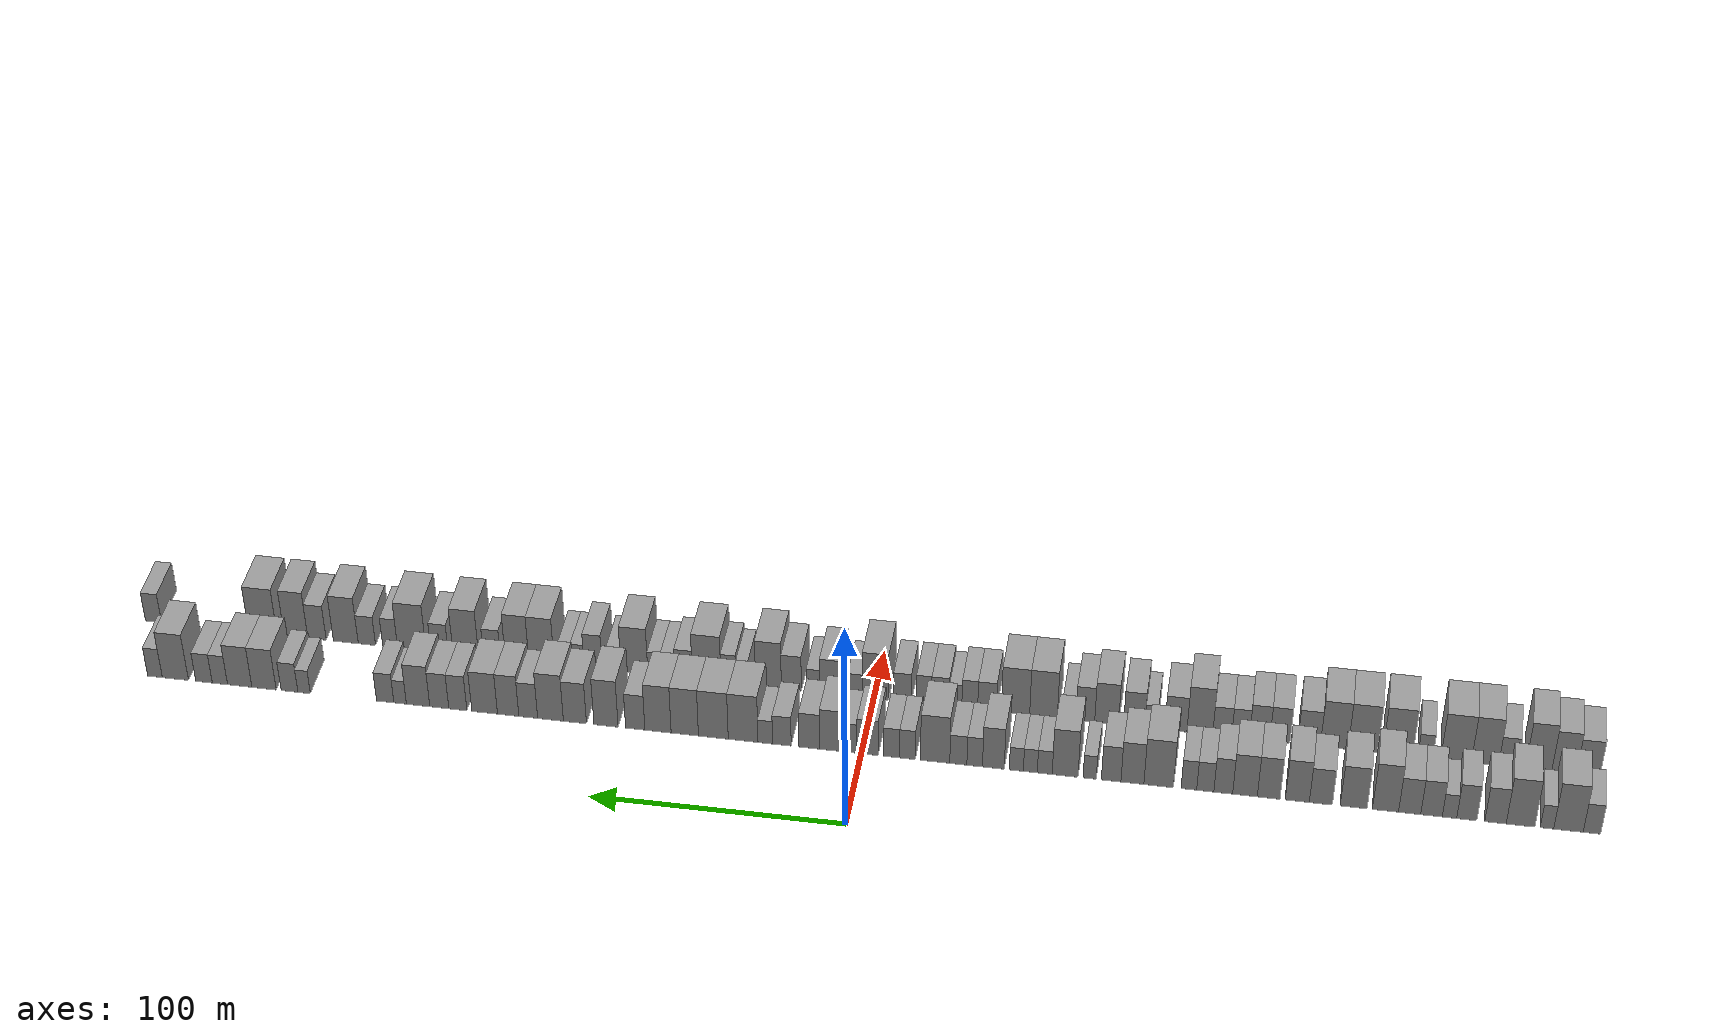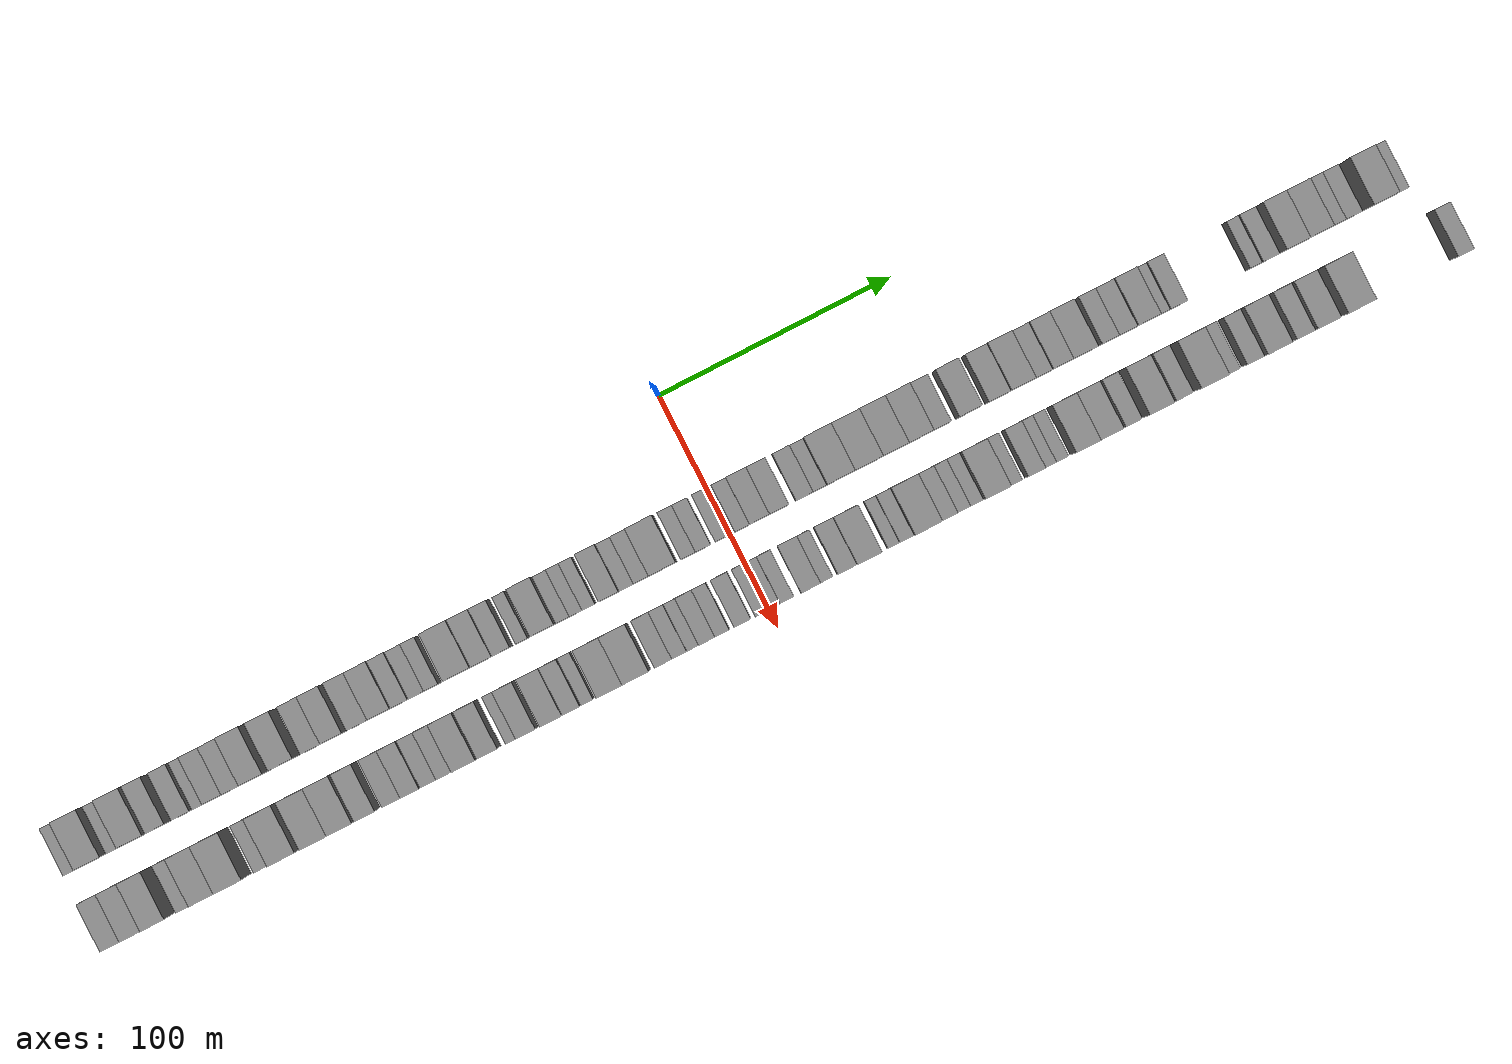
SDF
<sdf version="1.6">
 <world name="default">
  <scene>
   <sky><clouds><speed>12</speed></clouds></sky>
   <ambient>0.4 0.4 0.4 1</ambient>
   <background>0.7 0.7 0.7 1</background>
   <shadows>1</shadows>
  </scene>
  <gravity>0 0 -9.8066</gravity>
  <magnetic_field>6e-06 2.3e-05 -4.2e-05</magnetic_field>
  <physics default="0" name="default_physics" type="ode">
   <ode>
    <solver>
     <type>quick</type>
     <iters>10</iters>
     <sor>1.0</sor>
     <use_dynamic_moi_rescaling>0</use_dynamic_moi_rescaling>
    </solver>
    <constraints>
     <cfm>0</cfm>
     <erp>0.2</erp>
     <contact_max_correcting_vel>100</contact_max_correcting_vel>
     <contact_surface_layer>0.001</contact_surface_layer>
    </constraints>
   </ode>
   <max_step_size>0.004</max_step_size>
   <real_time_factor>1</real_time_factor>
   <real_time_update_rate>250</real_time_update_rate>
  </physics>
  <light name="sun" type="directional">
   <pose>0 0 10 0 0 0</pose>
   <diffuse>0.8 0.8 0.8 1</diffuse>
   <specular>0.2 0.2 0.2 1</specular>
   <attenuation>
    <range>1000</range>
    <constant>0.9</constant>
    <linear>0.01</linear>
    <quadratic>0.001</quadratic>
   </attenuation>
   <direction>-0.5 0.1 -0.9</direction>
  </light>
  <model name="building_1">
   <static>1</static>
   <pose>50.0000 -280.7285 0 0.000000 0.000000 0.000000</pose>
   <link name="link">
    <pose>0 0 7.50 0 0 0</pose>
    <collision name="collision"><geometry><box><size>20.0000 6.5430 15.0000</size></box></geometry></collision>
    <visual name="visual">
     <cast_shadows>0</cast_shadows>
     <geometry><box><size>20.0000 6.5430 15.0000</size></box></geometry>
     <material>
      <script>
       <uri>model://grey_wall/materials/scripts</uri>
       <uri>model://grey_wall/materials/textures</uri>
       <name>vrc/grey_wall</name>
      </script>
     </material>
    </visual>
   </link>
  </model>
  <model name="building_2">
   <static>1</static>
   <pose>50.0000 -271.9288 0 0.000000 0.000000 0.000000</pose>
   <link name="link">
    <pose>0 0 12.00 0 0 0</pose>
    <collision name="collision"><geometry><box><size>20.0000 11.0564 24.0000</size></box></geometry></collision>
    <visual name="visual">
     <cast_shadows>0</cast_shadows>
     <geometry><box><size>20.0000 11.0564 24.0000</size></box></geometry>
     <material>
      <script>
       <uri>model://grey_wall/materials/scripts</uri>
       <uri>model://grey_wall/materials/textures</uri>
       <name>vrc/grey_wall</name>
      </script>
     </material>
    </visual>
   </link>
  </model>
  <model name="building_3">
   <static>1</static>
   <pose>50.0000 -263.8461 0 0.000000 0.000000 0.000000</pose>
   <link name="link">
    <pose>0 0 6.00 0 0 0</pose>
    <collision name="collision"><geometry><box><size>20.0000 5.1090 12.0000</size></box></geometry></collision>
    <visual name="visual">
     <cast_shadows>0</cast_shadows>
     <geometry><box><size>20.0000 5.1090 12.0000</size></box></geometry>
     <material>
      <script>
       <uri>model://grey_wall/materials/scripts</uri>
       <uri>model://grey_wall/materials/textures</uri>
       <name>vrc/grey_wall</name>
      </script>
     </material>
    </visual>
   </link>
  </model>
  <model name="building_4">
   <static>1</static>
   <pose>50.0000 -253.8942 0 0.000000 0.000000 0.000000</pose>
   <link name="link">
    <pose>0 0 12.00 0 0 0</pose>
    <collision name="collision"><geometry><box><size>20.0000 10.7950 24.0000</size></box></geometry></collision>
    <visual name="visual">
     <cast_shadows>0</cast_shadows>
     <geometry><box><size>20.0000 10.7950 24.0000</size></box></geometry>
     <material>
      <script>
       <uri>model://grey_wall/materials/scripts</uri>
       <uri>model://grey_wall/materials/textures</uri>
       <name>vrc/grey_wall</name>
      </script>
     </material>
    </visual>
   </link>
  </model>
  <model name="building_5">
   <static>1</static>
   <pose>50.0000 -244.4497 0 0.000000 0.000000 0.000000</pose>
   <link name="link">
    <pose>0 0 9.00 0 0 0</pose>
    <collision name="collision"><geometry><box><size>20.0000 8.0939 18.0000</size></box></geometry></collision>
    <visual name="visual">
     <cast_shadows>0</cast_shadows>
     <geometry><box><size>20.0000 8.0939 18.0000</size></box></geometry>
     <material>
      <script>
       <uri>model://grey_wall/materials/scripts</uri>
       <uri>model://grey_wall/materials/textures</uri>
       <name>vrc/grey_wall</name>
      </script>
     </material>
    </visual>
   </link>
  </model>
  <model name="building_6">
   <static>1</static>
   <pose>50.0000 -233.5920 0 0.000000 0.000000 0.000000</pose>
   <link name="link">
    <pose>0 0 9.00 0 0 0</pose>
    <collision name="collision"><geometry><box><size>20.0000 7.6216 18.0000</size></box></geometry></collision>
    <visual name="visual">
     <cast_shadows>0</cast_shadows>
     <geometry><box><size>20.0000 7.6216 18.0000</size></box></geometry>
     <material>
      <script>
       <uri>model://grey_wall/materials/scripts</uri>
       <uri>model://grey_wall/materials/textures</uri>
       <name>vrc/grey_wall</name>
      </script>
     </material>
    </visual>
   </link>
  </model>
  <model name="building_7">
   <static>1</static>
   <pose>50.0000 -227.0531 0 0.000000 0.000000 0.000000</pose>
   <link name="link">
    <pose>0 0 6.00 0 0 0</pose>
    <collision name="collision"><geometry><box><size>20.0000 5.4563 12.0000</size></box></geometry></collision>
    <visual name="visual">
     <cast_shadows>0</cast_shadows>
     <geometry><box><size>20.0000 5.4563 12.0000</size></box></geometry>
     <material>
      <script>
       <uri>model://grey_wall/materials/scripts</uri>
       <uri>model://grey_wall/materials/textures</uri>
       <name>vrc/grey_wall</name>
      </script>
     </material>
    </visual>
   </link>
  </model>
  <model name="building_8">
   <static>1</static>
   <pose>50.0000 -220.2378 0 0.000000 0.000000 0.000000</pose>
   <link name="link">
    <pose>0 0 9.00 0 0 0</pose>
    <collision name="collision"><geometry><box><size>20.0000 8.1742 18.0000</size></box></geometry></collision>
    <visual name="visual">
     <cast_shadows>0</cast_shadows>
     <geometry><box><size>20.0000 8.1742 18.0000</size></box></geometry>
     <material>
      <script>
       <uri>model://grey_wall/materials/scripts</uri>
       <uri>model://grey_wall/materials/textures</uri>
       <name>vrc/grey_wall</name>
      </script>
     </material>
    </visual>
   </link>
  </model>
  <model name="building_9">
   <static>1</static>
   <pose>50.0000 -211.9330 0 0.000000 0.000000 0.000000</pose>
   <link name="link">
    <pose>0 0 9.00 0 0 0</pose>
    <collision name="collision"><geometry><box><size>20.0000 8.4355 18.0000</size></box></geometry></collision>
    <visual name="visual">
     <cast_shadows>0</cast_shadows>
     <geometry><box><size>20.0000 8.4355 18.0000</size></box></geometry>
     <material>
      <script>
       <uri>model://grey_wall/materials/scripts</uri>
       <uri>model://grey_wall/materials/textures</uri>
       <name>vrc/grey_wall</name>
      </script>
     </material>
    </visual>
   </link>
  </model>
  <model name="building_10">
   <static>1</static>
   <pose>50.0000 -202.7415 0 0.000000 0.000000 0.000000</pose>
   <link name="link">
    <pose>0 0 12.00 0 0 0</pose>
    <collision name="collision"><geometry><box><size>20.0000 9.9475 24.0000</size></box></geometry></collision>
    <visual name="visual">
     <cast_shadows>0</cast_shadows>
     <geometry><box><size>20.0000 9.9475 24.0000</size></box></geometry>
     <material>
      <script>
       <uri>model://grey_wall/materials/scripts</uri>
       <uri>model://grey_wall/materials/textures</uri>
       <name>vrc/grey_wall</name>
      </script>
     </material>
    </visual>
   </link>
  </model>
  <model name="building_11">
   <static>1</static>
   <pose>50.0000 -190.6426 0 0.000000 0.000000 0.000000</pose>
   <link name="link">
    <pose>0 0 10.50 0 0 0</pose>
    <collision name="collision"><geometry><box><size>20.0000 10.2502 21.0000</size></box></geometry></collision>
    <visual name="visual">
     <cast_shadows>0</cast_shadows>
     <geometry><box><size>20.0000 10.2502 21.0000</size></box></geometry>
     <material>
      <script>
       <uri>model://grey_wall/materials/scripts</uri>
       <uri>model://grey_wall/materials/textures</uri>
       <name>vrc/grey_wall</name>
      </script>
     </material>
    </visual>
   </link>
  </model>
  <model name="building_12">
   <static>1</static>
   <pose>50.0000 -178.1155 0 0.000000 0.000000 0.000000</pose>
   <link name="link">
    <pose>0 0 9.00 0 0 0</pose>
    <collision name="collision"><geometry><box><size>20.0000 8.8040 18.0000</size></box></geometry></collision>
    <visual name="visual">
     <cast_shadows>0</cast_shadows>
     <geometry><box><size>20.0000 8.8040 18.0000</size></box></geometry>
     <material>
      <script>
       <uri>model://grey_wall/materials/scripts</uri>
       <uri>model://grey_wall/materials/textures</uri>
       <name>vrc/grey_wall</name>
      </script>
     </material>
    </visual>
   </link>
  </model>
  <model name="building_13">
   <static>1</static>
   <pose>50.0000 -169.1064 0 0.000000 0.000000 0.000000</pose>
   <link name="link">
    <pose>0 0 10.50 0 0 0</pose>
    <collision name="collision"><geometry><box><size>20.0000 9.2141 21.0000</size></box></geometry></collision>
    <visual name="visual">
     <cast_shadows>0</cast_shadows>
     <geometry><box><size>20.0000 9.2141 21.0000</size></box></geometry>
     <material>
      <script>
       <uri>model://grey_wall/materials/scripts</uri>
       <uri>model://grey_wall/materials/textures</uri>
       <name>vrc/grey_wall</name>
      </script>
     </material>
    </visual>
   </link>
  </model>
  <model name="building_14">
   <static>1</static>
   <pose>50.0000 -158.1400 0 0.000000 0.000000 0.000000</pose>
   <link name="link">
    <pose>0 0 10.50 0 0 0</pose>
    <collision name="collision"><geometry><box><size>20.0000 8.7185 21.0000</size></box></geometry></collision>
    <visual name="visual">
     <cast_shadows>0</cast_shadows>
     <geometry><box><size>20.0000 8.7185 21.0000</size></box></geometry>
     <material>
      <script>
       <uri>model://grey_wall/materials/scripts</uri>
       <uri>model://grey_wall/materials/textures</uri>
       <name>vrc/grey_wall</name>
      </script>
     </material>
    </visual>
   </link>
  </model>
  <model name="building_15">
   <static>1</static>
   <pose>50.0000 -149.0470 0 0.000000 0.000000 0.000000</pose>
   <link name="link">
    <pose>0 0 10.50 0 0 0</pose>
    <collision name="collision"><geometry><box><size>20.0000 9.4675 21.0000</size></box></geometry></collision>
    <visual name="visual">
     <cast_shadows>0</cast_shadows>
     <geometry><box><size>20.0000 9.4675 21.0000</size></box></geometry>
     <material>
      <script>
       <uri>model://grey_wall/materials/scripts</uri>
       <uri>model://grey_wall/materials/textures</uri>
       <name>vrc/grey_wall</name>
      </script>
     </material>
    </visual>
   </link>
  </model>
  <model name="building_16">
   <static>1</static>
   <pose>50.0000 -140.7030 0 0.000000 0.000000 0.000000</pose>
   <link name="link">
    <pose>0 0 9.00 0 0 0</pose>
    <collision name="collision"><geometry><box><size>20.0000 7.2206 18.0000</size></box></geometry></collision>
    <visual name="visual">
     <cast_shadows>0</cast_shadows>
     <geometry><box><size>20.0000 7.2206 18.0000</size></box></geometry>
     <material>
      <script>
       <uri>model://grey_wall/materials/scripts</uri>
       <uri>model://grey_wall/materials/textures</uri>
       <name>vrc/grey_wall</name>
      </script>
     </material>
    </visual>
   </link>
  </model>
  <model name="building_17">
   <static>1</static>
   <pose>50.0000 -133.7853 0 0.000000 0.000000 0.000000</pose>
   <link name="link">
    <pose>0 0 7.50 0 0 0</pose>
    <collision name="collision"><geometry><box><size>20.0000 6.6148 15.0000</size></box></geometry></collision>
    <visual name="visual">
     <cast_shadows>0</cast_shadows>
     <geometry><box><size>20.0000 6.6148 15.0000</size></box></geometry>
     <material>
      <script>
       <uri>model://grey_wall/materials/scripts</uri>
       <uri>model://grey_wall/materials/textures</uri>
       <name>vrc/grey_wall</name>
      </script>
     </material>
    </visual>
   </link>
  </model>
  <model name="building_18">
   <static>1</static>
   <pose>50.0000 -127.4758 0 0.000000 0.000000 0.000000</pose>
   <link name="link">
    <pose>0 0 7.50 0 0 0</pose>
    <collision name="collision"><geometry><box><size>20.0000 6.0041 15.0000</size></box></geometry></collision>
    <visual name="visual">
     <cast_shadows>0</cast_shadows>
     <geometry><box><size>20.0000 6.0041 15.0000</size></box></geometry>
     <material>
      <script>
       <uri>model://grey_wall/materials/scripts</uri>
       <uri>model://grey_wall/materials/textures</uri>
       <name>vrc/grey_wall</name>
      </script>
     </material>
    </visual>
   </link>
  </model>
  <model name="building_19">
   <static>1</static>
   <pose>50.0000 -115.7782 0 0.000000 0.000000 0.000000</pose>
   <link name="link">
    <pose>0 0 12.00 0 0 0</pose>
    <collision name="collision"><geometry><box><size>20.0000 11.3912 24.0000</size></box></geometry></collision>
    <visual name="visual">
     <cast_shadows>0</cast_shadows>
     <geometry><box><size>20.0000 11.3912 24.0000</size></box></geometry>
     <material>
      <script>
       <uri>model://grey_wall/materials/scripts</uri>
       <uri>model://grey_wall/materials/textures</uri>
       <name>vrc/grey_wall</name>
      </script>
     </material>
    </visual>
   </link>
  </model>
  <model name="building_20">
   <static>1</static>
   <pose>50.0000 -105.6370 0 0.000000 0.000000 0.000000</pose>
   <link name="link">
    <pose>0 0 10.50 0 0 0</pose>
    <collision name="collision"><geometry><box><size>20.0000 8.8911 21.0000</size></box></geometry></collision>
    <visual name="visual">
     <cast_shadows>0</cast_shadows>
     <geometry><box><size>20.0000 8.8911 21.0000</size></box></geometry>
     <material>
      <script>
       <uri>model://grey_wall/materials/scripts</uri>
       <uri>model://grey_wall/materials/textures</uri>
       <name>vrc/grey_wall</name>
      </script>
     </material>
    </visual>
   </link>
  </model>
  <model name="building_21">
   <static>1</static>
   <pose>50.0000 -97.4049 0 0.000000 0.000000 0.000000</pose>
   <link name="link">
    <pose>0 0 9.00 0 0 0</pose>
    <collision name="collision"><geometry><box><size>20.0000 7.5730 18.0000</size></box></geometry></collision>
    <visual name="visual">
     <cast_shadows>0</cast_shadows>
     <geometry><box><size>20.0000 7.5730 18.0000</size></box></geometry>
     <material>
      <script>
       <uri>model://grey_wall/materials/scripts</uri>
       <uri>model://grey_wall/materials/textures</uri>
       <name>vrc/grey_wall</name>
      </script>
     </material>
    </visual>
   </link>
  </model>
  <model name="building_22">
   <static>1</static>
   <pose>50.0000 -89.0741 0 0.000000 0.000000 0.000000</pose>
   <link name="link">
    <pose>0 0 6.00 0 0 0</pose>
    <collision name="collision"><geometry><box><size>20.0000 5.0886 12.0000</size></box></geometry></collision>
    <visual name="visual">
     <cast_shadows>0</cast_shadows>
     <geometry><box><size>20.0000 5.0886 12.0000</size></box></geometry>
     <material>
      <script>
       <uri>model://grey_wall/materials/scripts</uri>
       <uri>model://grey_wall/materials/textures</uri>
       <name>vrc/grey_wall</name>
      </script>
     </material>
    </visual>
   </link>
  </model>
  <model name="building_23">
   <static>1</static>
   <pose>50.0000 -79.5198 0 0.000000 0.000000 0.000000</pose>
   <link name="link">
    <pose>0 0 12.00 0 0 0</pose>
    <collision name="collision"><geometry><box><size>20.0000 10.0201 24.0000</size></box></geometry></collision>
    <visual name="visual">
     <cast_shadows>0</cast_shadows>
     <geometry><box><size>20.0000 10.0201 24.0000</size></box></geometry>
     <material>
      <script>
       <uri>model://grey_wall/materials/scripts</uri>
       <uri>model://grey_wall/materials/textures</uri>
       <name>vrc/grey_wall</name>
      </script>
     </material>
    </visual>
   </link>
  </model>
  <model name="building_24">
   <static>1</static>
   <pose>50.0000 -71.6095 0 0.000000 0.000000 0.000000</pose>
   <link name="link">
    <pose>0 0 6.00 0 0 0</pose>
    <collision name="collision"><geometry><box><size>20.0000 5.8004 12.0000</size></box></geometry></collision>
    <visual name="visual">
     <cast_shadows>0</cast_shadows>
     <geometry><box><size>20.0000 5.8004 12.0000</size></box></geometry>
     <material>
      <script>
       <uri>model://grey_wall/materials/scripts</uri>
       <uri>model://grey_wall/materials/textures</uri>
       <name>vrc/grey_wall</name>
      </script>
     </material>
    </visual>
   </link>
  </model>
  <model name="building_25">
   <static>1</static>
   <pose>50.0000 -65.9958 0 0.000000 0.000000 0.000000</pose>
   <link name="link">
    <pose>0 0 6.00 0 0 0</pose>
    <collision name="collision"><geometry><box><size>20.0000 5.4270 12.0000</size></box></geometry></collision>
    <visual name="visual">
     <cast_shadows>0</cast_shadows>
     <geometry><box><size>20.0000 5.4270 12.0000</size></box></geometry>
     <material>
      <script>
       <uri>model://grey_wall/materials/scripts</uri>
       <uri>model://grey_wall/materials/textures</uri>
       <name>vrc/grey_wall</name>
      </script>
     </material>
    </visual>
   </link>
  </model>
  <model name="building_26">
   <static>1</static>
   <pose>50.0000 -60.5416 0 0.000000 0.000000 0.000000</pose>
   <link name="link">
    <pose>0 0 6.00 0 0 0</pose>
    <collision name="collision"><geometry><box><size>20.0000 5.4814 12.0000</size></box></geometry></collision>
    <visual name="visual">
     <cast_shadows>0</cast_shadows>
     <geometry><box><size>20.0000 5.4814 12.0000</size></box></geometry>
     <material>
      <script>
       <uri>model://grey_wall/materials/scripts</uri>
       <uri>model://grey_wall/materials/textures</uri>
       <name>vrc/grey_wall</name>
      </script>
     </material>
    </visual>
   </link>
  </model>
  <model name="building_27">
   <static>1</static>
   <pose>50.0000 -51.5552 0 0.000000 0.000000 0.000000</pose>
   <link name="link">
    <pose>0 0 10.50 0 0 0</pose>
    <collision name="collision"><geometry><box><size>20.0000 8.4914 21.0000</size></box></geometry></collision>
    <visual name="visual">
     <cast_shadows>0</cast_shadows>
     <geometry><box><size>20.0000 8.4914 21.0000</size></box></geometry>
     <material>
      <script>
       <uri>model://grey_wall/materials/scripts</uri>
       <uri>model://grey_wall/materials/textures</uri>
       <name>vrc/grey_wall</name>
      </script>
     </material>
    </visual>
   </link>
  </model>
  <model name="building_28">
   <static>1</static>
   <pose>50.0000 -44.2493 0 0.000000 0.000000 0.000000</pose>
   <link name="link">
    <pose>0 0 7.50 0 0 0</pose>
    <collision name="collision"><geometry><box><size>20.0000 6.1206 15.0000</size></box></geometry></collision>
    <visual name="visual">
     <cast_shadows>0</cast_shadows>
     <geometry><box><size>20.0000 6.1206 15.0000</size></box></geometry>
     <material>
      <script>
       <uri>model://grey_wall/materials/scripts</uri>
       <uri>model://grey_wall/materials/textures</uri>
       <name>vrc/grey_wall</name>
      </script>
     </material>
    </visual>
   </link>
  </model>
  <model name="building_29">
   <static>1</static>
   <pose>50.0000 -37.8376 0 0.000000 0.000000 0.000000</pose>
   <link name="link">
    <pose>0 0 7.50 0 0 0</pose>
    <collision name="collision"><geometry><box><size>20.0000 6.7027 15.0000</size></box></geometry></collision>
    <visual name="visual">
     <cast_shadows>0</cast_shadows>
     <geometry><box><size>20.0000 6.7027 15.0000</size></box></geometry>
     <material>
      <script>
       <uri>model://grey_wall/materials/scripts</uri>
       <uri>model://grey_wall/materials/textures</uri>
       <name>vrc/grey_wall</name>
      </script>
     </material>
    </visual>
   </link>
  </model>
  <model name="building_30">
   <static>1</static>
   <pose>50.0000 -28.7276 0 0.000000 0.000000 0.000000</pose>
   <link name="link">
    <pose>0 0 12.00 0 0 0</pose>
    <collision name="collision"><geometry><box><size>20.0000 11.5173 24.0000</size></box></geometry></collision>
    <visual name="visual">
     <cast_shadows>0</cast_shadows>
     <geometry><box><size>20.0000 11.5173 24.0000</size></box></geometry>
     <material>
      <script>
       <uri>model://grey_wall/materials/scripts</uri>
       <uri>model://grey_wall/materials/textures</uri>
       <name>vrc/grey_wall</name>
      </script>
     </material>
    </visual>
   </link>
  </model>
  <model name="building_31">
   <static>1</static>
   <pose>50.0000 -17.8754 0 0.000000 0.000000 0.000000</pose>
   <link name="link">
    <pose>0 0 7.50 0 0 0</pose>
    <collision name="collision"><geometry><box><size>20.0000 6.1872 15.0000</size></box></geometry></collision>
    <visual name="visual">
     <cast_shadows>0</cast_shadows>
     <geometry><box><size>20.0000 6.1872 15.0000</size></box></geometry>
     <material>
      <script>
       <uri>model://grey_wall/materials/scripts</uri>
       <uri>model://grey_wall/materials/textures</uri>
       <name>vrc/grey_wall</name>
      </script>
     </material>
    </visual>
   </link>
  </model>
  <model name="building_32">
   <static>1</static>
   <pose>50.0000 -11.5547 0 0.000000 0.000000 0.000000</pose>
   <link name="link">
    <pose>0 0 7.50 0 0 0</pose>
    <collision name="collision"><geometry><box><size>20.0000 6.4543 15.0000</size></box></geometry></collision>
    <visual name="visual">
     <cast_shadows>0</cast_shadows>
     <geometry><box><size>20.0000 6.4543 15.0000</size></box></geometry>
     <material>
      <script>
       <uri>model://grey_wall/materials/scripts</uri>
       <uri>model://grey_wall/materials/textures</uri>
       <name>vrc/grey_wall</name>
      </script>
     </material>
    </visual>
   </link>
  </model>
  <model name="building_33">
   <static>1</static>
   <pose>50.0000 -2.1452 0 0.000000 0.000000 0.000000</pose>
   <link name="link">
    <pose>0 0 9.00 0 0 0</pose>
    <collision name="collision"><geometry><box><size>20.0000 8.3647 18.0000</size></box></geometry></collision>
    <visual name="visual">
     <cast_shadows>0</cast_shadows>
     <geometry><box><size>20.0000 8.3647 18.0000</size></box></geometry>
     <material>
      <script>
       <uri>model://grey_wall/materials/scripts</uri>
       <uri>model://grey_wall/materials/textures</uri>
       <name>vrc/grey_wall</name>
      </script>
     </material>
    </visual>
   </link>
  </model>
  <model name="building_34">
   <static>1</static>
   <pose>50.0000 5.1659 0 0.000000 0.000000 0.000000</pose>
   <link name="link">
    <pose>0 0 7.50 0 0 0</pose>
    <collision name="collision"><geometry><box><size>20.0000 6.2576 15.0000</size></box></geometry></collision>
    <visual name="visual">
     <cast_shadows>0</cast_shadows>
     <geometry><box><size>20.0000 6.2576 15.0000</size></box></geometry>
     <material>
      <script>
       <uri>model://grey_wall/materials/scripts</uri>
       <uri>model://grey_wall/materials/textures</uri>
       <name>vrc/grey_wall</name>
      </script>
     </material>
    </visual>
   </link>
  </model>
  <model name="building_35">
   <static>1</static>
   <pose>50.0000 12.5445 0 0.000000 0.000000 0.000000</pose>
   <link name="link">
    <pose>0 0 10.50 0 0 0</pose>
    <collision name="collision"><geometry><box><size>20.0000 8.4996 21.0000</size></box></geometry></collision>
    <visual name="visual">
     <cast_shadows>0</cast_shadows>
     <geometry><box><size>20.0000 8.4996 21.0000</size></box></geometry>
     <material>
      <script>
       <uri>model://grey_wall/materials/scripts</uri>
       <uri>model://grey_wall/materials/textures</uri>
       <name>vrc/grey_wall</name>
      </script>
     </material>
    </visual>
   </link>
  </model>
  <model name="building_36">
   <static>1</static>
   <pose>50.0000 20.9216 0 0.000000 0.000000 0.000000</pose>
   <link name="link">
    <pose>0 0 9.00 0 0 0</pose>
    <collision name="collision"><geometry><box><size>20.0000 8.2547 18.0000</size></box></geometry></collision>
    <visual name="visual">
     <cast_shadows>0</cast_shadows>
     <geometry><box><size>20.0000 8.2547 18.0000</size></box></geometry>
     <material>
      <script>
       <uri>model://grey_wall/materials/scripts</uri>
       <uri>model://grey_wall/materials/textures</uri>
       <name>vrc/grey_wall</name>
      </script>
     </material>
    </visual>
   </link>
  </model>
  <model name="building_37">
   <static>1</static>
   <pose>50.0000 31.7448 0 0.000000 0.000000 0.000000</pose>
   <link name="link">
    <pose>0 0 7.50 0 0 0</pose>
    <collision name="collision"><geometry><box><size>20.0000 7.3918 15.0000</size></box></geometry></collision>
    <visual name="visual">
     <cast_shadows>0</cast_shadows>
     <geometry><box><size>20.0000 7.3918 15.0000</size></box></geometry>
     <material>
      <script>
       <uri>model://grey_wall/materials/scripts</uri>
       <uri>model://grey_wall/materials/textures</uri>
       <name>vrc/grey_wall</name>
      </script>
     </material>
    </visual>
   </link>
  </model>
  <model name="building_38">
   <static>1</static>
   <pose>50.0000 38.3287 0 0.000000 0.000000 0.000000</pose>
   <link name="link">
    <pose>0 0 6.00 0 0 0</pose>
    <collision name="collision"><geometry><box><size>20.0000 5.7759 12.0000</size></box></geometry></collision>
    <visual name="visual">
     <cast_shadows>0</cast_shadows>
     <geometry><box><size>20.0000 5.7759 12.0000</size></box></geometry>
     <material>
      <script>
       <uri>model://grey_wall/materials/scripts</uri>
       <uri>model://grey_wall/materials/textures</uri>
       <name>vrc/grey_wall</name>
      </script>
     </material>
    </visual>
   </link>
  </model>
  <model name="building_39">
   <static>1</static>
   <pose>50.0000 47.1344 0 0.000000 0.000000 0.000000</pose>
   <link name="link">
    <pose>0 0 12.00 0 0 0</pose>
    <collision name="collision"><geometry><box><size>20.0000 11.8356 24.0000</size></box></geometry></collision>
    <visual name="visual">
     <cast_shadows>0</cast_shadows>
     <geometry><box><size>20.0000 11.8356 24.0000</size></box></geometry>
     <material>
      <script>
       <uri>model://grey_wall/materials/scripts</uri>
       <uri>model://grey_wall/materials/textures</uri>
       <name>vrc/grey_wall</name>
      </script>
     </material>
    </visual>
   </link>
  </model>
  <model name="building_40">
   <static>1</static>
   <pose>50.0000 58.9942 0 0.000000 0.000000 0.000000</pose>
   <link name="link">
    <pose>0 0 12.00 0 0 0</pose>
    <collision name="collision"><geometry><box><size>20.0000 11.8840 24.0000</size></box></geometry></collision>
    <visual name="visual">
     <cast_shadows>0</cast_shadows>
     <geometry><box><size>20.0000 11.8840 24.0000</size></box></geometry>
     <material>
      <script>
       <uri>model://grey_wall/materials/scripts</uri>
       <uri>model://grey_wall/materials/textures</uri>
       <name>vrc/grey_wall</name>
      </script>
     </material>
    </visual>
   </link>
  </model>
  <model name="building_41">
   <static>1</static>
   <pose>50.0000 70.3936 0 0.000000 0.000000 0.000000</pose>
   <link name="link">
    <pose>0 0 12.00 0 0 0</pose>
    <collision name="collision"><geometry><box><size>20.0000 10.9147 24.0000</size></box></geometry></collision>
    <visual name="visual">
     <cast_shadows>0</cast_shadows>
     <geometry><box><size>20.0000 10.9147 24.0000</size></box></geometry>
     <material>
      <script>
       <uri>model://grey_wall/materials/scripts</uri>
       <uri>model://grey_wall/materials/textures</uri>
       <name>vrc/grey_wall</name>
      </script>
     </material>
    </visual>
   </link>
  </model>
  <model name="building_42">
   <static>1</static>
   <pose>50.0000 81.1011 0 0.000000 0.000000 0.000000</pose>
   <link name="link">
    <pose>0 0 12.00 0 0 0</pose>
    <collision name="collision"><geometry><box><size>20.0000 10.5003 24.0000</size></box></geometry></collision>
    <visual name="visual">
     <cast_shadows>0</cast_shadows>
     <geometry><box><size>20.0000 10.5003 24.0000</size></box></geometry>
     <material>
      <script>
       <uri>model://grey_wall/materials/scripts</uri>
       <uri>model://grey_wall/materials/textures</uri>
       <name>vrc/grey_wall</name>
      </script>
     </material>
    </visual>
   </link>
  </model>
  <model name="building_43">
   <static>1</static>
   <pose>50.0000 90.2170 0 0.000000 0.000000 0.000000</pose>
   <link name="link">
    <pose>0 0 9.00 0 0 0</pose>
    <collision name="collision"><geometry><box><size>20.0000 7.7314 18.0000</size></box></geometry></collision>
    <visual name="visual">
     <cast_shadows>0</cast_shadows>
     <geometry><box><size>20.0000 7.7314 18.0000</size></box></geometry>
     <material>
      <script>
       <uri>model://grey_wall/materials/scripts</uri>
       <uri>model://grey_wall/materials/textures</uri>
       <name>vrc/grey_wall</name>
      </script>
     </material>
    </visual>
   </link>
  </model>
  <model name="building_44">
   <static>1</static>
   <pose>50.0000 101.9413 0 0.000000 0.000000 0.000000</pose>
   <link name="link">
    <pose>0 0 12.00 0 0 0</pose>
    <collision name="collision"><geometry><box><size>20.0000 9.7173 24.0000</size></box></geometry></collision>
    <visual name="visual">
     <cast_shadows>0</cast_shadows>
     <geometry><box><size>20.0000 9.7173 24.0000</size></box></geometry>
     <material>
      <script>
       <uri>model://grey_wall/materials/scripts</uri>
       <uri>model://grey_wall/materials/textures</uri>
       <name>vrc/grey_wall</name>
      </script>
     </material>
    </visual>
   </link>
  </model>
  <model name="building_45">
   <static>1</static>
   <pose>50.0000 114.4521 0 0.000000 0.000000 0.000000</pose>
   <link name="link">
    <pose>0 0 10.50 0 0 0</pose>
    <collision name="collision"><geometry><box><size>20.0000 9.3042 21.0000</size></box></geometry></collision>
    <visual name="visual">
     <cast_shadows>0</cast_shadows>
     <geometry><box><size>20.0000 9.3042 21.0000</size></box></geometry>
     <material>
      <script>
       <uri>model://grey_wall/materials/scripts</uri>
       <uri>model://grey_wall/materials/textures</uri>
       <name>vrc/grey_wall</name>
      </script>
     </material>
    </visual>
   </link>
  </model>
  <model name="building_46">
   <static>1</static>
   <pose>50.0000 124.3024 0 0.000000 0.000000 0.000000</pose>
   <link name="link">
    <pose>0 0 12.00 0 0 0</pose>
    <collision name="collision"><geometry><box><size>20.0000 10.3964 24.0000</size></box></geometry></collision>
    <visual name="visual">
     <cast_shadows>0</cast_shadows>
     <geometry><box><size>20.0000 10.3964 24.0000</size></box></geometry>
     <material>
      <script>
       <uri>model://grey_wall/materials/scripts</uri>
       <uri>model://grey_wall/materials/textures</uri>
       <name>vrc/grey_wall</name>
      </script>
     </material>
    </visual>
   </link>
  </model>
  <model name="building_47">
   <static>1</static>
   <pose>50.0000 133.2978 0 0.000000 0.000000 0.000000</pose>
   <link name="link">
    <pose>0 0 9.00 0 0 0</pose>
    <collision name="collision"><geometry><box><size>20.0000 7.5946 18.0000</size></box></geometry></collision>
    <visual name="visual">
     <cast_shadows>0</cast_shadows>
     <geometry><box><size>20.0000 7.5946 18.0000</size></box></geometry>
     <material>
      <script>
       <uri>model://grey_wall/materials/scripts</uri>
       <uri>model://grey_wall/materials/textures</uri>
       <name>vrc/grey_wall</name>
      </script>
     </material>
    </visual>
   </link>
  </model>
  <model name="building_48">
   <static>1</static>
   <pose>50.0000 141.4103 0 0.000000 0.000000 0.000000</pose>
   <link name="link">
    <pose>0 0 10.50 0 0 0</pose>
    <collision name="collision"><geometry><box><size>20.0000 8.6304 21.0000</size></box></geometry></collision>
    <visual name="visual">
     <cast_shadows>0</cast_shadows>
     <geometry><box><size>20.0000 8.6304 21.0000</size></box></geometry>
     <material>
      <script>
       <uri>model://grey_wall/materials/scripts</uri>
       <uri>model://grey_wall/materials/textures</uri>
       <name>vrc/grey_wall</name>
      </script>
     </material>
    </visual>
   </link>
  </model>
  <model name="building_49">
   <static>1</static>
   <pose>50.0000 150.9284 0 0.000000 0.000000 0.000000</pose>
   <link name="link">
    <pose>0 0 10.50 0 0 0</pose>
    <collision name="collision"><geometry><box><size>20.0000 10.4057 21.0000</size></box></geometry></collision>
    <visual name="visual">
     <cast_shadows>0</cast_shadows>
     <geometry><box><size>20.0000 10.4057 21.0000</size></box></geometry>
     <material>
      <script>
       <uri>model://grey_wall/materials/scripts</uri>
       <uri>model://grey_wall/materials/textures</uri>
       <name>vrc/grey_wall</name>
      </script>
     </material>
    </visual>
   </link>
  </model>
  <model name="building_50">
   <static>1</static>
   <pose>50.0000 161.7996 0 0.000000 0.000000 0.000000</pose>
   <link name="link">
    <pose>0 0 9.00 0 0 0</pose>
    <collision name="collision"><geometry><box><size>20.0000 7.3368 18.0000</size></box></geometry></collision>
    <visual name="visual">
     <cast_shadows>0</cast_shadows>
     <geometry><box><size>20.0000 7.3368 18.0000</size></box></geometry>
     <material>
      <script>
       <uri>model://grey_wall/materials/scripts</uri>
       <uri>model://grey_wall/materials/textures</uri>
       <name>vrc/grey_wall</name>
      </script>
     </material>
    </visual>
   </link>
  </model>
  <model name="building_51">
   <static>1</static>
   <pose>50.0000 169.3375 0 0.000000 0.000000 0.000000</pose>
   <link name="link">
    <pose>0 0 9.00 0 0 0</pose>
    <collision name="collision"><geometry><box><size>20.0000 7.7389 18.0000</size></box></geometry></collision>
    <visual name="visual">
     <cast_shadows>0</cast_shadows>
     <geometry><box><size>20.0000 7.7389 18.0000</size></box></geometry>
     <material>
      <script>
       <uri>model://grey_wall/materials/scripts</uri>
       <uri>model://grey_wall/materials/textures</uri>
       <name>vrc/grey_wall</name>
      </script>
     </material>
    </visual>
   </link>
  </model>
  <model name="building_52">
   <static>1</static>
   <pose>50.0000 177.9718 0 0.000000 0.000000 0.000000</pose>
   <link name="link">
    <pose>0 0 10.50 0 0 0</pose>
    <collision name="collision"><geometry><box><size>20.0000 9.5297 21.0000</size></box></geometry></collision>
    <visual name="visual">
     <cast_shadows>0</cast_shadows>
     <geometry><box><size>20.0000 9.5297 21.0000</size></box></geometry>
     <material>
      <script>
       <uri>model://grey_wall/materials/scripts</uri>
       <uri>model://grey_wall/materials/textures</uri>
       <name>vrc/grey_wall</name>
      </script>
     </material>
    </visual>
   </link>
  </model>
  <model name="building_53">
   <static>1</static>
   <pose>50.0000 185.2828 0 0.000000 0.000000 0.000000</pose>
   <link name="link">
    <pose>0 0 6.00 0 0 0</pose>
    <collision name="collision"><geometry><box><size>20.0000 5.0922 12.0000</size></box></geometry></collision>
    <visual name="visual">
     <cast_shadows>0</cast_shadows>
     <geometry><box><size>20.0000 5.0922 12.0000</size></box></geometry>
     <material>
      <script>
       <uri>model://grey_wall/materials/scripts</uri>
       <uri>model://grey_wall/materials/textures</uri>
       <name>vrc/grey_wall</name>
      </script>
     </material>
    </visual>
   </link>
  </model>
  <model name="building_54">
   <static>1</static>
   <pose>50.0000 191.3628 0 0.000000 0.000000 0.000000</pose>
   <link name="link">
    <pose>0 0 7.50 0 0 0</pose>
    <collision name="collision"><geometry><box><size>20.0000 7.0677 15.0000</size></box></geometry></collision>
    <visual name="visual">
     <cast_shadows>0</cast_shadows>
     <geometry><box><size>20.0000 7.0677 15.0000</size></box></geometry>
     <material>
      <script>
       <uri>model://grey_wall/materials/scripts</uri>
       <uri>model://grey_wall/materials/textures</uri>
       <name>vrc/grey_wall</name>
      </script>
     </material>
    </visual>
   </link>
  </model>
  <model name="building_55">
   <static>1</static>
   <pose>50.0000 224.5762 0 0.000000 0.000000 0.000000</pose>
   <link name="link">
    <pose>0 0 6.00 0 0 0</pose>
    <collision name="collision"><geometry><box><size>20.0000 5.1197 12.0000</size></box></geometry></collision>
    <visual name="visual">
     <cast_shadows>0</cast_shadows>
     <geometry><box><size>20.0000 5.1197 12.0000</size></box></geometry>
     <material>
      <script>
       <uri>model://grey_wall/materials/scripts</uri>
       <uri>model://grey_wall/materials/textures</uri>
       <name>vrc/grey_wall</name>
      </script>
     </material>
    </visual>
   </link>
  </model>
  <model name="building_56">
   <static>1</static>
   <pose>50.0000 230.5793 0 0.000000 0.000000 0.000000</pose>
   <link name="link">
    <pose>0 0 7.50 0 0 0</pose>
    <collision name="collision"><geometry><box><size>20.0000 6.8864 15.0000</size></box></geometry></collision>
    <visual name="visual">
     <cast_shadows>0</cast_shadows>
     <geometry><box><size>20.0000 6.8864 15.0000</size></box></geometry>
     <material>
      <script>
       <uri>model://grey_wall/materials/scripts</uri>
       <uri>model://grey_wall/materials/textures</uri>
       <name>vrc/grey_wall</name>
      </script>
     </material>
    </visual>
   </link>
  </model>
  <model name="building_57">
   <static>1</static>
   <pose>50.0000 241.0453 0 0.000000 0.000000 0.000000</pose>
   <link name="link">
    <pose>0 0 10.50 0 0 0</pose>
    <collision name="collision"><geometry><box><size>20.0000 10.0457 21.0000</size></box></geometry></collision>
    <visual name="visual">
     <cast_shadows>0</cast_shadows>
     <geometry><box><size>20.0000 10.0457 21.0000</size></box></geometry>
     <material>
      <script>
       <uri>model://grey_wall/materials/scripts</uri>
       <uri>model://grey_wall/materials/textures</uri>
       <name>vrc/grey_wall</name>
      </script>
     </material>
    </visual>
   </link>
  </model>
  <model name="building_58">
   <static>1</static>
   <pose>50.0000 251.0858 0 0.000000 0.000000 0.000000</pose>
   <link name="link">
    <pose>0 0 10.50 0 0 0</pose>
    <collision name="collision"><geometry><box><size>20.0000 10.0353 21.0000</size></box></geometry></collision>
    <visual name="visual">
     <cast_shadows>0</cast_shadows>
     <geometry><box><size>20.0000 10.0353 21.0000</size></box></geometry>
     <material>
      <script>
       <uri>model://grey_wall/materials/scripts</uri>
       <uri>model://grey_wall/materials/textures</uri>
       <name>vrc/grey_wall</name>
      </script>
     </material>
    </visual>
   </link>
  </model>
  <model name="building_59">
   <static>1</static>
   <pose>50.0000 259.2685 0 0.000000 0.000000 0.000000</pose>
   <link name="link">
    <pose>0 0 7.50 0 0 0</pose>
    <collision name="collision"><geometry><box><size>20.0000 6.3301 15.0000</size></box></geometry></collision>
    <visual name="visual">
     <cast_shadows>0</cast_shadows>
     <geometry><box><size>20.0000 6.3301 15.0000</size></box></geometry>
     <material>
      <script>
       <uri>model://grey_wall/materials/scripts</uri>
       <uri>model://grey_wall/materials/textures</uri>
       <name>vrc/grey_wall</name>
      </script>
     </material>
    </visual>
   </link>
  </model>
  <model name="building_60">
   <static>1</static>
   <pose>50.0000 265.8349 0 0.000000 0.000000 0.000000</pose>
   <link name="link">
    <pose>0 0 7.50 0 0 0</pose>
    <collision name="collision"><geometry><box><size>20.0000 6.8027 15.0000</size></box></geometry></collision>
    <visual name="visual">
     <cast_shadows>0</cast_shadows>
     <geometry><box><size>20.0000 6.8027 15.0000</size></box></geometry>
     <material>
      <script>
       <uri>model://grey_wall/materials/scripts</uri>
       <uri>model://grey_wall/materials/textures</uri>
       <name>vrc/grey_wall</name>
      </script>
     </material>
    </visual>
   </link>
  </model>
  <model name="building_61">
   <static>1</static>
   <pose>50.0000 277.6647 0 0.000000 0.000000 0.000000</pose>
   <link name="link">
    <pose>0 0 12.00 0 0 0</pose>
    <collision name="collision"><geometry><box><size>20.0000 10.8569 24.0000</size></box></geometry></collision>
    <visual name="visual">
     <cast_shadows>0</cast_shadows>
     <geometry><box><size>20.0000 10.8569 24.0000</size></box></geometry>
     <material>
      <script>
       <uri>model://grey_wall/materials/scripts</uri>
       <uri>model://grey_wall/materials/textures</uri>
       <name>vrc/grey_wall</name>
      </script>
     </material>
    </visual>
   </link>
  </model>
  <model name="building_62">
   <static>1</static>
   <pose>50.0000 286.1082 0 0.000000 0.000000 0.000000</pose>
   <link name="link">
    <pose>0 0 7.50 0 0 0</pose>
    <collision name="collision"><geometry><box><size>20.0000 6.0302 15.0000</size></box></geometry></collision>
    <visual name="visual">
     <cast_shadows>0</cast_shadows>
     <geometry><box><size>20.0000 6.0302 15.0000</size></box></geometry>
     <material>
      <script>
       <uri>model://grey_wall/materials/scripts</uri>
       <uri>model://grey_wall/materials/textures</uri>
       <name>vrc/grey_wall</name>
      </script>
     </material>
    </visual>
   </link>
  </model>
  <model name="building_63">
   <static>1</static>
   <pose>82.0000 -279.5156 0 0.000000 0.000000 0.000000</pose>
   <link name="link">
    <pose>0 0 9.00 0 0 0</pose>
    <collision name="collision"><geometry><box><size>20.0000 8.9687 18.0000</size></box></geometry></collision>
    <visual name="visual">
     <cast_shadows>0</cast_shadows>
     <geometry><box><size>20.0000 8.9687 18.0000</size></box></geometry>
     <material>
      <script>
       <uri>model://grey_wall/materials/scripts</uri>
       <uri>model://grey_wall/materials/textures</uri>
       <name>vrc/grey_wall</name>
      </script>
     </material>
    </visual>
   </link>
  </model>
  <model name="building_64">
   <static>1</static>
   <pose>82.0000 -270.2996 0 0.000000 0.000000 0.000000</pose>
   <link name="link">
    <pose>0 0 10.50 0 0 0</pose>
    <collision name="collision"><geometry><box><size>20.0000 9.4635 21.0000</size></box></geometry></collision>
    <visual name="visual">
     <cast_shadows>0</cast_shadows>
     <geometry><box><size>20.0000 9.4635 21.0000</size></box></geometry>
     <material>
      <script>
       <uri>model://grey_wall/materials/scripts</uri>
       <uri>model://grey_wall/materials/textures</uri>
       <name>vrc/grey_wall</name>
      </script>
     </material>
    </visual>
   </link>
  </model>
  <model name="building_65">
   <static>1</static>
   <pose>82.0000 -260.5115 0 0.000000 0.000000 0.000000</pose>
   <link name="link">
    <pose>0 0 12.00 0 0 0</pose>
    <collision name="collision"><geometry><box><size>20.0000 10.1127 24.0000</size></box></geometry></collision>
    <visual name="visual">
     <cast_shadows>0</cast_shadows>
     <geometry><box><size>20.0000 10.1127 24.0000</size></box></geometry>
     <material>
      <script>
       <uri>model://grey_wall/materials/scripts</uri>
       <uri>model://grey_wall/materials/textures</uri>
       <name>vrc/grey_wall</name>
      </script>
     </material>
    </visual>
   </link>
  </model>
  <model name="building_66">
   <static>1</static>
   <pose>82.0000 -248.8087 0 0.000000 0.000000 0.000000</pose>
   <link name="link">
    <pose>0 0 7.50 0 0 0</pose>
    <collision name="collision"><geometry><box><size>20.0000 7.2929 15.0000</size></box></geometry></collision>
    <visual name="visual">
     <cast_shadows>0</cast_shadows>
     <geometry><box><size>20.0000 7.2929 15.0000</size></box></geometry>
     <material>
      <script>
       <uri>model://grey_wall/materials/scripts</uri>
       <uri>model://grey_wall/materials/textures</uri>
       <name>vrc/grey_wall</name>
      </script>
     </material>
    </visual>
   </link>
  </model>
  <model name="building_67">
   <static>1</static>
   <pose>82.0000 -239.9047 0 0.000000 0.000000 0.000000</pose>
   <link name="link">
    <pose>0 0 12.00 0 0 0</pose>
    <collision name="collision"><geometry><box><size>20.0000 10.5150 24.0000</size></box></geometry></collision>
    <visual name="visual">
     <cast_shadows>0</cast_shadows>
     <geometry><box><size>20.0000 10.5150 24.0000</size></box></geometry>
     <material>
      <script>
       <uri>model://grey_wall/materials/scripts</uri>
       <uri>model://grey_wall/materials/textures</uri>
       <name>vrc/grey_wall</name>
      </script>
     </material>
    </visual>
   </link>
  </model>
  <model name="building_68">
   <static>1</static>
   <pose>82.0000 -228.7389 0 0.000000 0.000000 0.000000</pose>
   <link name="link">
    <pose>0 0 12.00 0 0 0</pose>
    <collision name="collision"><geometry><box><size>20.0000 11.8166 24.0000</size></box></geometry></collision>
    <visual name="visual">
     <cast_shadows>0</cast_shadows>
     <geometry><box><size>20.0000 11.8166 24.0000</size></box></geometry>
     <material>
      <script>
       <uri>model://grey_wall/materials/scripts</uri>
       <uri>model://grey_wall/materials/textures</uri>
       <name>vrc/grey_wall</name>
      </script>
     </material>
    </visual>
   </link>
  </model>
  <model name="building_69">
   <static>1</static>
   <pose>82.0000 -216.9084 0 0.000000 0.000000 0.000000</pose>
   <link name="link">
    <pose>0 0 6.00 0 0 0</pose>
    <collision name="collision"><geometry><box><size>20.0000 5.8445 12.0000</size></box></geometry></collision>
    <visual name="visual">
     <cast_shadows>0</cast_shadows>
     <geometry><box><size>20.0000 5.8445 12.0000</size></box></geometry>
     <material>
      <script>
       <uri>model://grey_wall/materials/scripts</uri>
       <uri>model://grey_wall/materials/textures</uri>
       <name>vrc/grey_wall</name>
      </script>
     </material>
    </visual>
   </link>
  </model>
  <model name="building_70">
   <static>1</static>
   <pose>82.0000 -206.1798 0 0.000000 0.000000 0.000000</pose>
   <link name="link">
    <pose>0 0 12.00 0 0 0</pose>
    <collision name="collision"><geometry><box><size>20.0000 11.6127 24.0000</size></box></geometry></collision>
    <visual name="visual">
     <cast_shadows>0</cast_shadows>
     <geometry><box><size>20.0000 11.6127 24.0000</size></box></geometry>
     <material>
      <script>
       <uri>model://grey_wall/materials/scripts</uri>
       <uri>model://grey_wall/materials/textures</uri>
       <name>vrc/grey_wall</name>
      </script>
     </material>
    </visual>
   </link>
  </model>
  <model name="building_71">
   <static>1</static>
   <pose>82.0000 -192.6436 0 0.000000 0.000000 0.000000</pose>
   <link name="link">
    <pose>0 0 12.00 0 0 0</pose>
    <collision name="collision"><geometry><box><size>20.0000 11.4597 24.0000</size></box></geometry></collision>
    <visual name="visual">
     <cast_shadows>0</cast_shadows>
     <geometry><box><size>20.0000 11.4597 24.0000</size></box></geometry>
     <material>
      <script>
       <uri>model://grey_wall/materials/scripts</uri>
       <uri>model://grey_wall/materials/textures</uri>
       <name>vrc/grey_wall</name>
      </script>
     </material>
    </visual>
   </link>
  </model>
  <model name="building_72">
   <static>1</static>
   <pose>82.0000 -181.5321 0 0.000000 0.000000 0.000000</pose>
   <link name="link">
    <pose>0 0 12.00 0 0 0</pose>
    <collision name="collision"><geometry><box><size>20.0000 10.7633 24.0000</size></box></geometry></collision>
    <visual name="visual">
     <cast_shadows>0</cast_shadows>
     <geometry><box><size>20.0000 10.7633 24.0000</size></box></geometry>
     <material>
      <script>
       <uri>model://grey_wall/materials/scripts</uri>
       <uri>model://grey_wall/materials/textures</uri>
       <name>vrc/grey_wall</name>
      </script>
     </material>
    </visual>
   </link>
  </model>
  <model name="building_73">
   <static>1</static>
   <pose>82.0000 -171.7453 0 0.000000 0.000000 0.000000</pose>
   <link name="link">
    <pose>0 0 9.00 0 0 0</pose>
    <collision name="collision"><geometry><box><size>20.0000 8.8104 18.0000</size></box></geometry></collision>
    <visual name="visual">
     <cast_shadows>0</cast_shadows>
     <geometry><box><size>20.0000 8.8104 18.0000</size></box></geometry>
     <material>
      <script>
       <uri>model://grey_wall/materials/scripts</uri>
       <uri>model://grey_wall/materials/textures</uri>
       <name>vrc/grey_wall</name>
      </script>
     </material>
    </visual>
   </link>
  </model>
  <model name="building_74">
   <static>1</static>
   <pose>82.0000 -160.4064 0 0.000000 0.000000 0.000000</pose>
   <link name="link">
    <pose>0 0 9.00 0 0 0</pose>
    <collision name="collision"><geometry><box><size>20.0000 7.8674 18.0000</size></box></geometry></collision>
    <visual name="visual">
     <cast_shadows>0</cast_shadows>
     <geometry><box><size>20.0000 7.8674 18.0000</size></box></geometry>
     <material>
      <script>
       <uri>model://grey_wall/materials/scripts</uri>
       <uri>model://grey_wall/materials/textures</uri>
       <name>vrc/grey_wall</name>
      </script>
     </material>
    </visual>
   </link>
  </model>
  <model name="building_75">
   <static>1</static>
   <pose>82.0000 -152.4900 0 0.000000 0.000000 0.000000</pose>
   <link name="link">
    <pose>0 0 9.00 0 0 0</pose>
    <collision name="collision"><geometry><box><size>20.0000 7.9653 18.0000</size></box></geometry></collision>
    <visual name="visual">
     <cast_shadows>0</cast_shadows>
     <geometry><box><size>20.0000 7.9653 18.0000</size></box></geometry>
     <material>
      <script>
       <uri>model://grey_wall/materials/scripts</uri>
       <uri>model://grey_wall/materials/textures</uri>
       <name>vrc/grey_wall</name>
      </script>
     </material>
    </visual>
   </link>
  </model>
  <model name="building_76">
   <static>1</static>
   <pose>82.0000 -145.0527 0 0.000000 0.000000 0.000000</pose>
   <link name="link">
    <pose>0 0 7.50 0 0 0</pose>
    <collision name="collision"><geometry><box><size>20.0000 6.9092 15.0000</size></box></geometry></collision>
    <visual name="visual">
     <cast_shadows>0</cast_shadows>
     <geometry><box><size>20.0000 6.9092 15.0000</size></box></geometry>
     <material>
      <script>
       <uri>model://grey_wall/materials/scripts</uri>
       <uri>model://grey_wall/materials/textures</uri>
       <name>vrc/grey_wall</name>
      </script>
     </material>
    </visual>
   </link>
  </model>
  <model name="building_77">
   <static>1</static>
   <pose>82.0000 -137.8877 0 0.000000 0.000000 0.000000</pose>
   <link name="link">
    <pose>0 0 7.50 0 0 0</pose>
    <collision name="collision"><geometry><box><size>20.0000 7.4210 15.0000</size></box></geometry></collision>
    <visual name="visual">
     <cast_shadows>0</cast_shadows>
     <geometry><box><size>20.0000 7.4210 15.0000</size></box></geometry>
     <material>
      <script>
       <uri>model://grey_wall/materials/scripts</uri>
       <uri>model://grey_wall/materials/textures</uri>
       <name>vrc/grey_wall</name>
      </script>
     </material>
    </visual>
   </link>
  </model>
  <model name="building_78">
   <static>1</static>
   <pose>82.0000 -129.1051 0 0.000000 0.000000 0.000000</pose>
   <link name="link">
    <pose>0 0 12.00 0 0 0</pose>
    <collision name="collision"><geometry><box><size>20.0000 10.1441 24.0000</size></box></geometry></collision>
    <visual name="visual">
     <cast_shadows>0</cast_shadows>
     <geometry><box><size>20.0000 10.1441 24.0000</size></box></geometry>
     <material>
      <script>
       <uri>model://grey_wall/materials/scripts</uri>
       <uri>model://grey_wall/materials/textures</uri>
       <name>vrc/grey_wall</name>
      </script>
     </material>
    </visual>
   </link>
  </model>
  <model name="building_79">
   <static>1</static>
   <pose>82.0000 -119.6662 0 0.000000 0.000000 0.000000</pose>
   <link name="link">
    <pose>0 0 9.00 0 0 0</pose>
    <collision name="collision"><geometry><box><size>20.0000 8.7337 18.0000</size></box></geometry></collision>
    <visual name="visual">
     <cast_shadows>0</cast_shadows>
     <geometry><box><size>20.0000 8.7337 18.0000</size></box></geometry>
     <material>
      <script>
       <uri>model://grey_wall/materials/scripts</uri>
       <uri>model://grey_wall/materials/textures</uri>
       <name>vrc/grey_wall</name>
      </script>
     </material>
    </visual>
   </link>
  </model>
  <model name="building_80">
   <static>1</static>
   <pose>82.0000 -109.8791 0 0.000000 0.000000 0.000000</pose>
   <link name="link">
    <pose>0 0 6.00 0 0 0</pose>
    <collision name="collision"><geometry><box><size>20.0000 4.8406 12.0000</size></box></geometry></collision>
    <visual name="visual">
     <cast_shadows>0</cast_shadows>
     <geometry><box><size>20.0000 4.8406 12.0000</size></box></geometry>
     <material>
      <script>
       <uri>model://grey_wall/materials/scripts</uri>
       <uri>model://grey_wall/materials/textures</uri>
       <name>vrc/grey_wall</name>
      </script>
     </material>
    </visual>
   </link>
  </model>
  <model name="building_81">
   <static>1</static>
   <pose>82.0000 -103.2753 0 0.000000 0.000000 0.000000</pose>
   <link name="link">
    <pose>0 0 9.00 0 0 0</pose>
    <collision name="collision"><geometry><box><size>20.0000 8.3670 18.0000</size></box></geometry></collision>
    <visual name="visual">
     <cast_shadows>0</cast_shadows>
     <geometry><box><size>20.0000 8.3670 18.0000</size></box></geometry>
     <material>
      <script>
       <uri>model://grey_wall/materials/scripts</uri>
       <uri>model://grey_wall/materials/textures</uri>
       <name>vrc/grey_wall</name>
      </script>
     </material>
    </visual>
   </link>
  </model>
  <model name="building_82">
   <static>1</static>
   <pose>82.0000 -92.3901 0 0.000000 0.000000 0.000000</pose>
   <link name="link">
    <pose>0 0 10.50 0 0 0</pose>
    <collision name="collision"><geometry><box><size>20.0000 9.4034 21.0000</size></box></geometry></collision>
    <visual name="visual">
     <cast_shadows>0</cast_shadows>
     <geometry><box><size>20.0000 9.4034 21.0000</size></box></geometry>
     <material>
      <script>
       <uri>model://grey_wall/materials/scripts</uri>
       <uri>model://grey_wall/materials/textures</uri>
       <name>vrc/grey_wall</name>
      </script>
     </material>
    </visual>
   </link>
  </model>
  <model name="building_83">
   <static>1</static>
   <pose>82.0000 -83.9384 0 0.000000 0.000000 0.000000</pose>
   <link name="link">
    <pose>0 0 9.00 0 0 0</pose>
    <collision name="collision"><geometry><box><size>20.0000 7.5000 18.0000</size></box></geometry></collision>
    <visual name="visual">
     <cast_shadows>0</cast_shadows>
     <geometry><box><size>20.0000 7.5000 18.0000</size></box></geometry>
     <material>
      <script>
       <uri>model://grey_wall/materials/scripts</uri>
       <uri>model://grey_wall/materials/textures</uri>
       <name>vrc/grey_wall</name>
      </script>
     </material>
    </visual>
   </link>
  </model>
  <model name="building_84">
   <static>1</static>
   <pose>82.0000 -77.5324 0 0.000000 0.000000 0.000000</pose>
   <link name="link">
    <pose>0 0 6.00 0 0 0</pose>
    <collision name="collision"><geometry><box><size>20.0000 5.3120 12.0000</size></box></geometry></collision>
    <visual name="visual">
     <cast_shadows>0</cast_shadows>
     <geometry><box><size>20.0000 5.3120 12.0000</size></box></geometry>
     <material>
      <script>
       <uri>model://grey_wall/materials/scripts</uri>
       <uri>model://grey_wall/materials/textures</uri>
       <name>vrc/grey_wall</name>
      </script>
     </material>
    </visual>
   </link>
  </model>
  <model name="building_85">
   <static>1</static>
   <pose>82.0000 -67.4004 0 0.000000 0.000000 0.000000</pose>
   <link name="link">
    <pose>0 0 12.00 0 0 0</pose>
    <collision name="collision"><geometry><box><size>20.0000 10.9521 24.0000</size></box></geometry></collision>
    <visual name="visual">
     <cast_shadows>0</cast_shadows>
     <geometry><box><size>20.0000 10.9521 24.0000</size></box></geometry>
     <material>
      <script>
       <uri>model://grey_wall/materials/scripts</uri>
       <uri>model://grey_wall/materials/textures</uri>
       <name>vrc/grey_wall</name>
      </script>
     </material>
    </visual>
   </link>
  </model>
  <model name="building_86">
   <static>1</static>
   <pose>82.0000 -56.2996 0 0.000000 0.000000 0.000000</pose>
   <link name="link">
    <pose>0 0 12.00 0 0 0</pose>
    <collision name="collision"><geometry><box><size>20.0000 11.2494 24.0000</size></box></geometry></collision>
    <visual name="visual">
     <cast_shadows>0</cast_shadows>
     <geometry><box><size>20.0000 11.2494 24.0000</size></box></geometry>
     <material>
      <script>
       <uri>model://grey_wall/materials/scripts</uri>
       <uri>model://grey_wall/materials/textures</uri>
       <name>vrc/grey_wall</name>
      </script>
     </material>
    </visual>
   </link>
  </model>
  <model name="building_87">
   <static>1</static>
   <pose>82.0000 -44.9537 0 0.000000 0.000000 0.000000</pose>
   <link name="link">
    <pose>0 0 7.50 0 0 0</pose>
    <collision name="collision"><geometry><box><size>20.0000 7.4425 15.0000</size></box></geometry></collision>
    <visual name="visual">
     <cast_shadows>0</cast_shadows>
     <geometry><box><size>20.0000 7.4425 15.0000</size></box></geometry>
     <material>
      <script>
       <uri>model://grey_wall/materials/scripts</uri>
       <uri>model://grey_wall/materials/textures</uri>
       <name>vrc/grey_wall</name>
      </script>
     </material>
    </visual>
   </link>
  </model>
  <model name="building_88">
   <static>1</static>
   <pose>82.0000 -38.0687 0 0.000000 0.000000 0.000000</pose>
   <link name="link">
    <pose>0 0 7.50 0 0 0</pose>
    <collision name="collision"><geometry><box><size>20.0000 6.3276 15.0000</size></box></geometry></collision>
    <visual name="visual">
     <cast_shadows>0</cast_shadows>
     <geometry><box><size>20.0000 6.3276 15.0000</size></box></geometry>
     <material>
      <script>
       <uri>model://grey_wall/materials/scripts</uri>
       <uri>model://grey_wall/materials/textures</uri>
       <name>vrc/grey_wall</name>
      </script>
     </material>
    </visual>
   </link>
  </model>
  <model name="building_89">
   <static>1</static>
   <pose>82.0000 -32.3458 0 0.000000 0.000000 0.000000</pose>
   <link name="link">
    <pose>0 0 6.00 0 0 0</pose>
    <collision name="collision"><geometry><box><size>20.0000 5.1181 12.0000</size></box></geometry></collision>
    <visual name="visual">
     <cast_shadows>0</cast_shadows>
     <geometry><box><size>20.0000 5.1181 12.0000</size></box></geometry>
     <material>
      <script>
       <uri>model://grey_wall/materials/scripts</uri>
       <uri>model://grey_wall/materials/textures</uri>
       <name>vrc/grey_wall</name>
      </script>
     </material>
    </visual>
   </link>
  </model>
  <model name="building_90">
   <static>1</static>
   <pose>82.0000 -26.2811 0 0.000000 0.000000 0.000000</pose>
   <link name="link">
    <pose>0 0 7.50 0 0 0</pose>
    <collision name="collision"><geometry><box><size>20.0000 7.0113 15.0000</size></box></geometry></collision>
    <visual name="visual">
     <cast_shadows>0</cast_shadows>
     <geometry><box><size>20.0000 7.0113 15.0000</size></box></geometry>
     <material>
      <script>
       <uri>model://grey_wall/materials/scripts</uri>
       <uri>model://grey_wall/materials/textures</uri>
       <name>vrc/grey_wall</name>
      </script>
     </material>
    </visual>
   </link>
  </model>
  <model name="building_91">
   <static>1</static>
   <pose>82.0000 -19.7338 0 0.000000 0.000000 0.000000</pose>
   <link name="link">
    <pose>0 0 7.50 0 0 0</pose>
    <collision name="collision"><geometry><box><size>20.0000 6.0832 15.0000</size></box></geometry></collision>
    <visual name="visual">
     <cast_shadows>0</cast_shadows>
     <geometry><box><size>20.0000 6.0832 15.0000</size></box></geometry>
     <material>
      <script>
       <uri>model://grey_wall/materials/scripts</uri>
       <uri>model://grey_wall/materials/textures</uri>
       <name>vrc/grey_wall</name>
      </script>
     </material>
    </visual>
   </link>
  </model>
  <model name="building_92">
   <static>1</static>
   <pose>82.0000 -11.1395 0 0.000000 0.000000 0.000000</pose>
   <link name="link">
    <pose>0 0 7.50 0 0 0</pose>
    <collision name="collision"><geometry><box><size>20.0000 7.1054 15.0000</size></box></geometry></collision>
    <visual name="visual">
     <cast_shadows>0</cast_shadows>
     <geometry><box><size>20.0000 7.1054 15.0000</size></box></geometry>
     <material>
      <script>
       <uri>model://grey_wall/materials/scripts</uri>
       <uri>model://grey_wall/materials/textures</uri>
       <name>vrc/grey_wall</name>
      </script>
     </material>
    </visual>
   </link>
  </model>
  <model name="building_93">
   <static>1</static>
   <pose>82.0000 -0.3200 0 0.000000 0.000000 0.000000</pose>
   <link name="link">
    <pose>0 0 12.00 0 0 0</pose>
    <collision name="collision"><geometry><box><size>20.0000 10.5335 24.0000</size></box></geometry></collision>
    <visual name="visual">
     <cast_shadows>0</cast_shadows>
     <geometry><box><size>20.0000 10.5335 24.0000</size></box></geometry>
     <material>
      <script>
       <uri>model://grey_wall/materials/scripts</uri>
       <uri>model://grey_wall/materials/textures</uri>
       <name>vrc/grey_wall</name>
      </script>
     </material>
    </visual>
   </link>
  </model>
  <model name="building_94">
   <static>1</static>
   <pose>82.0000 7.8883 0 0.000000 0.000000 0.000000</pose>
   <link name="link">
    <pose>0 0 6.00 0 0 0</pose>
    <collision name="collision"><geometry><box><size>20.0000 5.8832 12.0000</size></box></geometry></collision>
    <visual name="visual">
     <cast_shadows>0</cast_shadows>
     <geometry><box><size>20.0000 5.8832 12.0000</size></box></geometry>
     <material>
      <script>
       <uri>model://grey_wall/materials/scripts</uri>
       <uri>model://grey_wall/materials/textures</uri>
       <name>vrc/grey_wall</name>
      </script>
     </material>
    </visual>
   </link>
  </model>
  <model name="building_95">
   <static>1</static>
   <pose>82.0000 17.9751 0 0.000000 0.000000 0.000000</pose>
   <link name="link">
    <pose>0 0 9.00 0 0 0</pose>
    <collision name="collision"><geometry><box><size>20.0000 8.2902 18.0000</size></box></geometry></collision>
    <visual name="visual">
     <cast_shadows>0</cast_shadows>
     <geometry><box><size>20.0000 8.2902 18.0000</size></box></geometry>
     <material>
      <script>
       <uri>model://grey_wall/materials/scripts</uri>
       <uri>model://grey_wall/materials/textures</uri>
       <name>vrc/grey_wall</name>
      </script>
     </material>
    </visual>
   </link>
  </model>
  <model name="building_96">
   <static>1</static>
   <pose>82.0000 24.7980 0 0.000000 0.000000 0.000000</pose>
   <link name="link">
    <pose>0 0 6.00 0 0 0</pose>
    <collision name="collision"><geometry><box><size>20.0000 5.3557 12.0000</size></box></geometry></collision>
    <visual name="visual">
     <cast_shadows>0</cast_shadows>
     <geometry><box><size>20.0000 5.3557 12.0000</size></box></geometry>
     <material>
      <script>
       <uri>model://grey_wall/materials/scripts</uri>
       <uri>model://grey_wall/materials/textures</uri>
       <name>vrc/grey_wall</name>
      </script>
     </material>
    </visual>
   </link>
  </model>
  <model name="building_97">
   <static>1</static>
   <pose>82.0000 33.5134 0 0.000000 0.000000 0.000000</pose>
   <link name="link">
    <pose>0 0 9.00 0 0 0</pose>
    <collision name="collision"><geometry><box><size>20.0000 8.0751 18.0000</size></box></geometry></collision>
    <visual name="visual">
     <cast_shadows>0</cast_shadows>
     <geometry><box><size>20.0000 8.0751 18.0000</size></box></geometry>
     <material>
      <script>
       <uri>model://grey_wall/materials/scripts</uri>
       <uri>model://grey_wall/materials/textures</uri>
       <name>vrc/grey_wall</name>
      </script>
     </material>
    </visual>
   </link>
  </model>
  <model name="building_98">
   <static>1</static>
   <pose>82.0000 42.7894 0 0.000000 0.000000 0.000000</pose>
   <link name="link">
    <pose>0 0 12.00 0 0 0</pose>
    <collision name="collision"><geometry><box><size>20.0000 10.4771 24.0000</size></box></geometry></collision>
    <visual name="visual">
     <cast_shadows>0</cast_shadows>
     <geometry><box><size>20.0000 10.4771 24.0000</size></box></geometry>
     <material>
      <script>
       <uri>model://grey_wall/materials/scripts</uri>
       <uri>model://grey_wall/materials/textures</uri>
       <name>vrc/grey_wall</name>
      </script>
     </material>
    </visual>
   </link>
  </model>
  <model name="building_99">
   <static>1</static>
   <pose>82.0000 53.4756 0 0.000000 0.000000 0.000000</pose>
   <link name="link">
    <pose>0 0 6.00 0 0 0</pose>
    <collision name="collision"><geometry><box><size>20.0000 4.8952 12.0000</size></box></geometry></collision>
    <visual name="visual">
     <cast_shadows>0</cast_shadows>
     <geometry><box><size>20.0000 4.8952 12.0000</size></box></geometry>
     <material>
      <script>
       <uri>model://grey_wall/materials/scripts</uri>
       <uri>model://grey_wall/materials/textures</uri>
       <name>vrc/grey_wall</name>
      </script>
     </material>
    </visual>
   </link>
  </model>
  <model name="building_100">
   <static>1</static>
   <pose>82.0000 58.9572 0 0.000000 0.000000 0.000000</pose>
   <link name="link">
    <pose>0 0 7.50 0 0 0</pose>
    <collision name="collision"><geometry><box><size>20.0000 6.0681 15.0000</size></box></geometry></collision>
    <visual name="visual">
     <cast_shadows>0</cast_shadows>
     <geometry><box><size>20.0000 6.0681 15.0000</size></box></geometry>
     <material>
      <script>
       <uri>model://grey_wall/materials/scripts</uri>
       <uri>model://grey_wall/materials/textures</uri>
       <name>vrc/grey_wall</name>
      </script>
     </material>
    </visual>
   </link>
  </model>
  <model name="building_101">
   <static>1</static>
   <pose>82.0000 67.7943 0 0.000000 0.000000 0.000000</pose>
   <link name="link">
    <pose>0 0 12.00 0 0 0</pose>
    <collision name="collision"><geometry><box><size>20.0000 11.6060 24.0000</size></box></geometry></collision>
    <visual name="visual">
     <cast_shadows>0</cast_shadows>
     <geometry><box><size>20.0000 11.6060 24.0000</size></box></geometry>
     <material>
      <script>
       <uri>model://grey_wall/materials/scripts</uri>
       <uri>model://grey_wall/materials/textures</uri>
       <name>vrc/grey_wall</name>
      </script>
     </material>
    </visual>
   </link>
  </model>
  <model name="building_102">
   <static>1</static>
   <pose>82.0000 77.1590 0 0.000000 0.000000 0.000000</pose>
   <link name="link">
    <pose>0 0 7.50 0 0 0</pose>
    <collision name="collision"><geometry><box><size>20.0000 7.1234 15.0000</size></box></geometry></collision>
    <visual name="visual">
     <cast_shadows>0</cast_shadows>
     <geometry><box><size>20.0000 7.1234 15.0000</size></box></geometry>
     <material>
      <script>
       <uri>model://grey_wall/materials/scripts</uri>
       <uri>model://grey_wall/materials/textures</uri>
       <name>vrc/grey_wall</name>
      </script>
     </material>
    </visual>
   </link>
  </model>
  <model name="building_103">
   <static>1</static>
   <pose>82.0000 83.5299 0 0.000000 0.000000 0.000000</pose>
   <link name="link">
    <pose>0 0 6.00 0 0 0</pose>
    <collision name="collision"><geometry><box><size>20.0000 5.6184 12.0000</size></box></geometry></collision>
    <visual name="visual">
     <cast_shadows>0</cast_shadows>
     <geometry><box><size>20.0000 5.6184 12.0000</size></box></geometry>
     <material>
      <script>
       <uri>model://grey_wall/materials/scripts</uri>
       <uri>model://grey_wall/materials/textures</uri>
       <name>vrc/grey_wall</name>
      </script>
     </material>
    </visual>
   </link>
  </model>
  <model name="building_104">
   <static>1</static>
   <pose>82.0000 89.0374 0 0.000000 0.000000 0.000000</pose>
   <link name="link">
    <pose>0 0 6.00 0 0 0</pose>
    <collision name="collision"><geometry><box><size>20.0000 5.3967 12.0000</size></box></geometry></collision>
    <visual name="visual">
     <cast_shadows>0</cast_shadows>
     <geometry><box><size>20.0000 5.3967 12.0000</size></box></geometry>
     <material>
      <script>
       <uri>model://grey_wall/materials/scripts</uri>
       <uri>model://grey_wall/materials/textures</uri>
       <name>vrc/grey_wall</name>
      </script>
     </material>
    </visual>
   </link>
  </model>
  <model name="building_105">
   <static>1</static>
   <pose>82.0000 97.2078 0 0.000000 0.000000 0.000000</pose>
   <link name="link">
    <pose>0 0 12.00 0 0 0</pose>
    <collision name="collision"><geometry><box><size>20.0000 10.9441 24.0000</size></box></geometry></collision>
    <visual name="visual">
     <cast_shadows>0</cast_shadows>
     <geometry><box><size>20.0000 10.9441 24.0000</size></box></geometry>
     <material>
      <script>
       <uri>model://grey_wall/materials/scripts</uri>
       <uri>model://grey_wall/materials/textures</uri>
       <name>vrc/grey_wall</name>
      </script>
     </material>
    </visual>
   </link>
  </model>
  <model name="building_106">
   <static>1</static>
   <pose>82.0000 105.5469 0 0.000000 0.000000 0.000000</pose>
   <link name="link">
    <pose>0 0 6.00 0 0 0</pose>
    <collision name="collision"><geometry><box><size>20.0000 5.7340 12.0000</size></box></geometry></collision>
    <visual name="visual">
     <cast_shadows>0</cast_shadows>
     <geometry><box><size>20.0000 5.7340 12.0000</size></box></geometry>
     <material>
      <script>
       <uri>model://grey_wall/materials/scripts</uri>
       <uri>model://grey_wall/materials/textures</uri>
       <name>vrc/grey_wall</name>
      </script>
     </material>
    </visual>
   </link>
  </model>
  <model name="building_107">
   <static>1</static>
   <pose>82.0000 114.1042 0 0.000000 0.000000 0.000000</pose>
   <link name="link">
    <pose>0 0 9.00 0 0 0</pose>
    <collision name="collision"><geometry><box><size>20.0000 7.3806 18.0000</size></box></geometry></collision>
    <visual name="visual">
     <cast_shadows>0</cast_shadows>
     <geometry><box><size>20.0000 7.3806 18.0000</size></box></geometry>
     <material>
      <script>
       <uri>model://grey_wall/materials/scripts</uri>
       <uri>model://grey_wall/materials/textures</uri>
       <name>vrc/grey_wall</name>
      </script>
     </material>
    </visual>
   </link>
  </model>
  <model name="building_108">
   <static>1</static>
   <pose>82.0000 120.3796 0 0.000000 0.000000 0.000000</pose>
   <link name="link">
    <pose>0 0 6.00 0 0 0</pose>
    <collision name="collision"><geometry><box><size>20.0000 5.1702 12.0000</size></box></geometry></collision>
    <visual name="visual">
     <cast_shadows>0</cast_shadows>
     <geometry><box><size>20.0000 5.1702 12.0000</size></box></geometry>
     <material>
      <script>
       <uri>model://grey_wall/materials/scripts</uri>
       <uri>model://grey_wall/materials/textures</uri>
       <name>vrc/grey_wall</name>
      </script>
     </material>
    </visual>
   </link>
  </model>
  <model name="building_109">
   <static>1</static>
   <pose>82.0000 125.5265 0 0.000000 0.000000 0.000000</pose>
   <link name="link">
    <pose>0 0 6.00 0 0 0</pose>
    <collision name="collision"><geometry><box><size>20.0000 5.1237 12.0000</size></box></geometry></collision>
    <visual name="visual">
     <cast_shadows>0</cast_shadows>
     <geometry><box><size>20.0000 5.1237 12.0000</size></box></geometry>
     <material>
      <script>
       <uri>model://grey_wall/materials/scripts</uri>
       <uri>model://grey_wall/materials/textures</uri>
       <name>vrc/grey_wall</name>
      </script>
     </material>
    </visual>
   </link>
  </model>
  <model name="building_110">
   <static>1</static>
   <pose>82.0000 135.2935 0 0.000000 0.000000 0.000000</pose>
   <link name="link">
    <pose>0 0 12.00 0 0 0</pose>
    <collision name="collision"><geometry><box><size>20.0000 10.4103 24.0000</size></box></geometry></collision>
    <visual name="visual">
     <cast_shadows>0</cast_shadows>
     <geometry><box><size>20.0000 10.4103 24.0000</size></box></geometry>
     <material>
      <script>
       <uri>model://grey_wall/materials/scripts</uri>
       <uri>model://grey_wall/materials/textures</uri>
       <name>vrc/grey_wall</name>
      </script>
     </material>
    </visual>
   </link>
  </model>
  <model name="building_111">
   <static>1</static>
   <pose>82.0000 145.3542 0 0.000000 0.000000 0.000000</pose>
   <link name="link">
    <pose>0 0 12.00 0 0 0</pose>
    <collision name="collision"><geometry><box><size>20.0000 9.7109 24.0000</size></box></geometry></collision>
    <visual name="visual">
     <cast_shadows>0</cast_shadows>
     <geometry><box><size>20.0000 9.7109 24.0000</size></box></geometry>
     <material>
      <script>
       <uri>model://grey_wall/materials/scripts</uri>
       <uri>model://grey_wall/materials/textures</uri>
       <name>vrc/grey_wall</name>
      </script>
     </material>
    </visual>
   </link>
  </model>
  <model name="building_112">
   <static>1</static>
   <pose>82.0000 155.7086 0 0.000000 0.000000 0.000000</pose>
   <link name="link">
    <pose>0 0 7.50 0 0 0</pose>
    <collision name="collision"><geometry><box><size>20.0000 6.9978 15.0000</size></box></geometry></collision>
    <visual name="visual">
     <cast_shadows>0</cast_shadows>
     <geometry><box><size>20.0000 6.9978 15.0000</size></box></geometry>
     <material>
      <script>
       <uri>model://grey_wall/materials/scripts</uri>
       <uri>model://grey_wall/materials/textures</uri>
       <name>vrc/grey_wall</name>
      </script>
     </material>
    </visual>
   </link>
  </model>
  <model name="building_113">
   <static>1</static>
   <pose>82.0000 166.5020 0 0.000000 0.000000 0.000000</pose>
   <link name="link">
    <pose>0 0 12.00 0 0 0</pose>
    <collision name="collision"><geometry><box><size>20.0000 10.5891 24.0000</size></box></geometry></collision>
    <visual name="visual">
     <cast_shadows>0</cast_shadows>
     <geometry><box><size>20.0000 10.5891 24.0000</size></box></geometry>
     <material>
      <script>
       <uri>model://grey_wall/materials/scripts</uri>
       <uri>model://grey_wall/materials/textures</uri>
       <name>vrc/grey_wall</name>
      </script>
     </material>
    </visual>
   </link>
  </model>
  <model name="building_114">
   <static>1</static>
   <pose>82.0000 177.3890 0 0.000000 0.000000 0.000000</pose>
   <link name="link">
    <pose>0 0 7.50 0 0 0</pose>
    <collision name="collision"><geometry><box><size>20.0000 7.1849 15.0000</size></box></geometry></collision>
    <visual name="visual">
     <cast_shadows>0</cast_shadows>
     <geometry><box><size>20.0000 7.1849 15.0000</size></box></geometry>
     <material>
      <script>
       <uri>model://grey_wall/materials/scripts</uri>
       <uri>model://grey_wall/materials/textures</uri>
       <name>vrc/grey_wall</name>
      </script>
     </material>
    </visual>
   </link>
  </model>
  <model name="building_115">
   <static>1</static>
   <pose>82.0000 188.8886 0 0.000000 0.000000 0.000000</pose>
   <link name="link">
    <pose>0 0 12.00 0 0 0</pose>
    <collision name="collision"><geometry><box><size>20.0000 11.8142 24.0000</size></box></geometry></collision>
    <visual name="visual">
     <cast_shadows>0</cast_shadows>
     <geometry><box><size>20.0000 11.8142 24.0000</size></box></geometry>
     <material>
      <script>
       <uri>model://grey_wall/materials/scripts</uri>
       <uri>model://grey_wall/materials/textures</uri>
       <name>vrc/grey_wall</name>
      </script>
     </material>
    </visual>
   </link>
  </model>
  <model name="building_116">
   <static>1</static>
   <pose>82.0000 197.8862 0 0.000000 0.000000 0.000000</pose>
   <link name="link">
    <pose>0 0 7.50 0 0 0</pose>
    <collision name="collision"><geometry><box><size>20.0000 6.1809 15.0000</size></box></geometry></collision>
    <visual name="visual">
     <cast_shadows>0</cast_shadows>
     <geometry><box><size>20.0000 6.1809 15.0000</size></box></geometry>
     <material>
      <script>
       <uri>model://grey_wall/materials/scripts</uri>
       <uri>model://grey_wall/materials/textures</uri>
       <name>vrc/grey_wall</name>
      </script>
     </material>
    </visual>
   </link>
  </model>
  <model name="building_117">
   <static>1</static>
   <pose>82.0000 207.5832 0 0.000000 0.000000 0.000000</pose>
   <link name="link">
    <pose>0 0 7.50 0 0 0</pose>
    <collision name="collision"><geometry><box><size>20.0000 7.2133 15.0000</size></box></geometry></collision>
    <visual name="visual">
     <cast_shadows>0</cast_shadows>
     <geometry><box><size>20.0000 7.2133 15.0000</size></box></geometry>
     <material>
      <script>
       <uri>model://grey_wall/materials/scripts</uri>
       <uri>model://grey_wall/materials/textures</uri>
       <name>vrc/grey_wall</name>
      </script>
     </material>
    </visual>
   </link>
  </model>
  <model name="building_118">
   <static>1</static>
   <pose>82.0000 216.3632 0 0.000000 0.000000 0.000000</pose>
   <link name="link">
    <pose>0 0 12.00 0 0 0</pose>
    <collision name="collision"><geometry><box><size>20.0000 10.3466 24.0000</size></box></geometry></collision>
    <visual name="visual">
     <cast_shadows>0</cast_shadows>
     <geometry><box><size>20.0000 10.3466 24.0000</size></box></geometry>
     <material>
      <script>
       <uri>model://grey_wall/materials/scripts</uri>
       <uri>model://grey_wall/materials/textures</uri>
       <name>vrc/grey_wall</name>
      </script>
     </material>
    </visual>
   </link>
  </model>
  <model name="building_119">
   <static>1</static>
   <pose>82.0000 228.3818 0 0.000000 0.000000 0.000000</pose>
   <link name="link">
    <pose>0 0 9.00 0 0 0</pose>
    <collision name="collision"><geometry><box><size>20.0000 7.6907 18.0000</size></box></geometry></collision>
    <visual name="visual">
     <cast_shadows>0</cast_shadows>
     <geometry><box><size>20.0000 7.6907 18.0000</size></box></geometry>
     <material>
      <script>
       <uri>model://grey_wall/materials/scripts</uri>
       <uri>model://grey_wall/materials/textures</uri>
       <name>vrc/grey_wall</name>
      </script>
     </material>
    </visual>
   </link>
  </model>
  <model name="building_120">
   <static>1</static>
   <pose>82.0000 237.1584 0 0.000000 0.000000 0.000000</pose>
   <link name="link">
    <pose>0 0 12.00 0 0 0</pose>
    <collision name="collision"><geometry><box><size>20.0000 9.8624 24.0000</size></box></geometry></collision>
    <visual name="visual">
     <cast_shadows>0</cast_shadows>
     <geometry><box><size>20.0000 9.8624 24.0000</size></box></geometry>
     <material>
      <script>
       <uri>model://grey_wall/materials/scripts</uri>
       <uri>model://grey_wall/materials/textures</uri>
       <name>vrc/grey_wall</name>
      </script>
     </material>
    </visual>
   </link>
  </model>
  <model name="building_121">
   <static>1</static>
   <pose>82.0000 251.0252 0 0.000000 0.000000 0.000000</pose>
   <link name="link">
    <pose>0 0 12.00 0 0 0</pose>
    <collision name="collision"><geometry><box><size>20.0000 11.8711 24.0000</size></box></geometry></collision>
    <visual name="visual">
     <cast_shadows>0</cast_shadows>
     <geometry><box><size>20.0000 11.8711 24.0000</size></box></geometry>
     <material>
      <script>
       <uri>model://grey_wall/materials/scripts</uri>
       <uri>model://grey_wall/materials/textures</uri>
       <name>vrc/grey_wall</name>
      </script>
     </material>
    </visual>
   </link>
  </model>
  <model name="building_122">
   <static>1</static>
   <pose>82.0000 297.1240 0 0.000000 0.000000 0.000000</pose>
   <link name="link">
    <pose>0 0 7.50 0 0 0</pose>
    <collision name="collision"><geometry><box><size>20.0000 6.7755 15.0000</size></box></geometry></collision>
    <visual name="visual">
     <cast_shadows>0</cast_shadows>
     <geometry><box><size>20.0000 6.7755 15.0000</size></box></geometry>
     <material>
      <script>
       <uri>model://grey_wall/materials/scripts</uri>
       <uri>model://grey_wall/materials/textures</uri>
       <name>vrc/grey_wall</name>
      </script>
     </material>
    </visual>
   </link>
  </model>
 </world>
</sdf>
